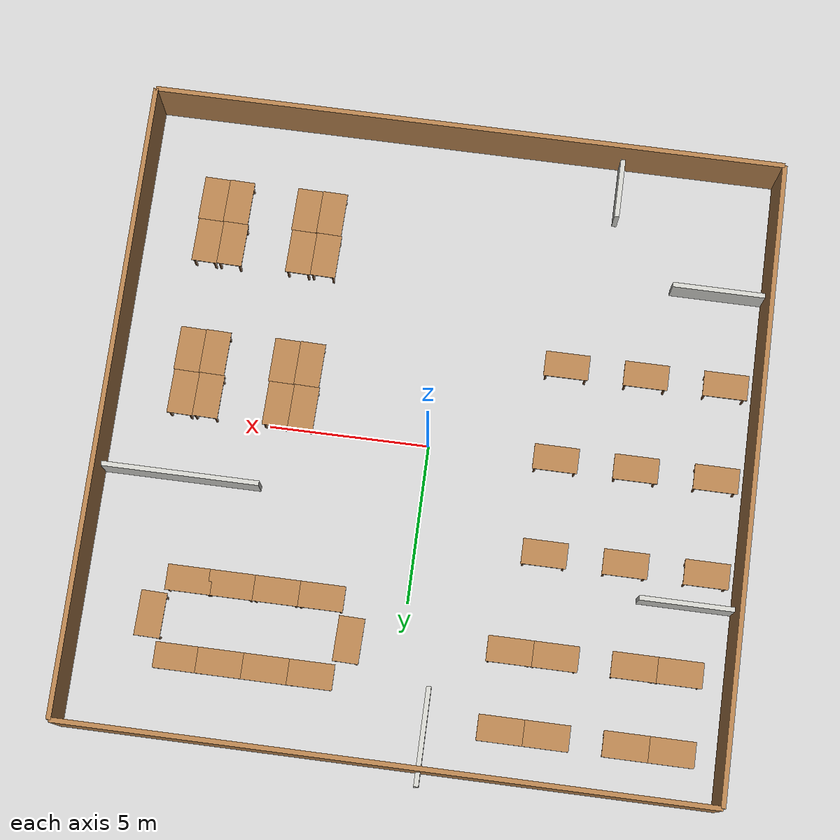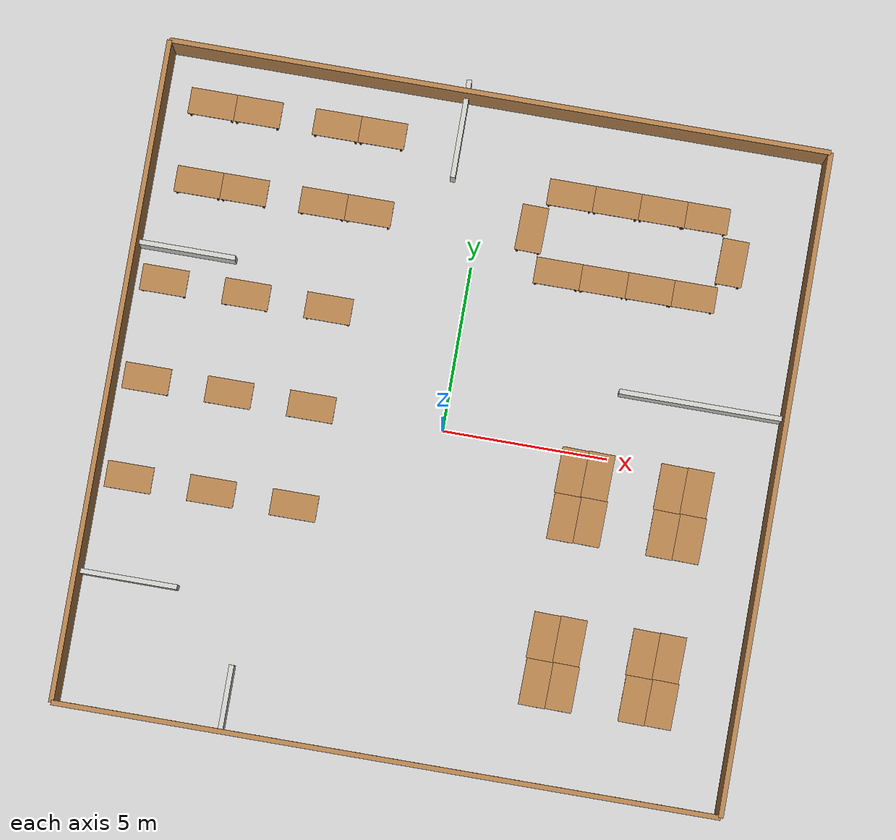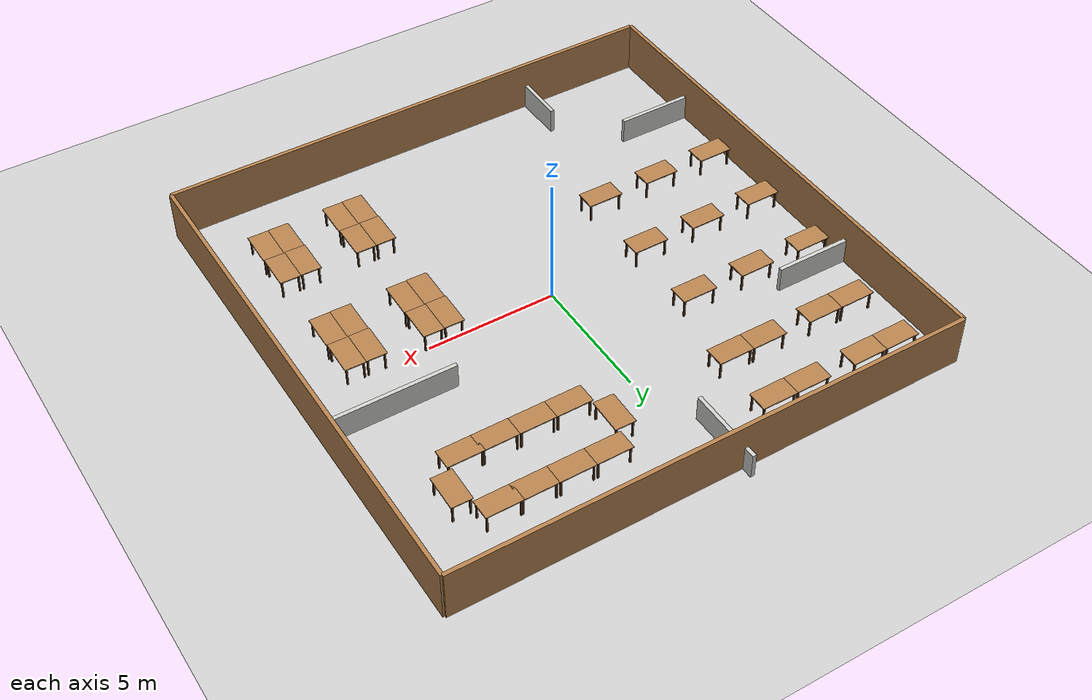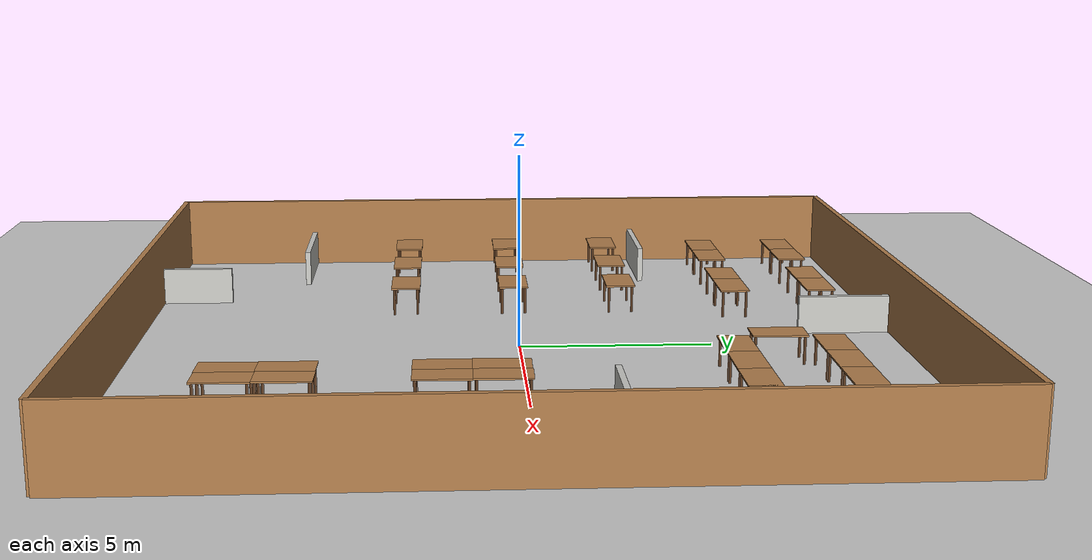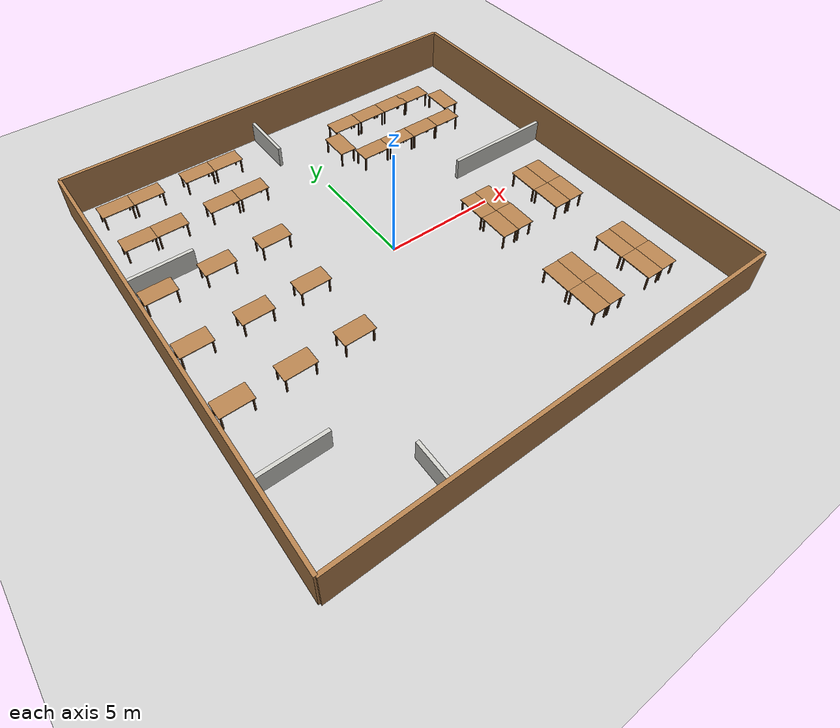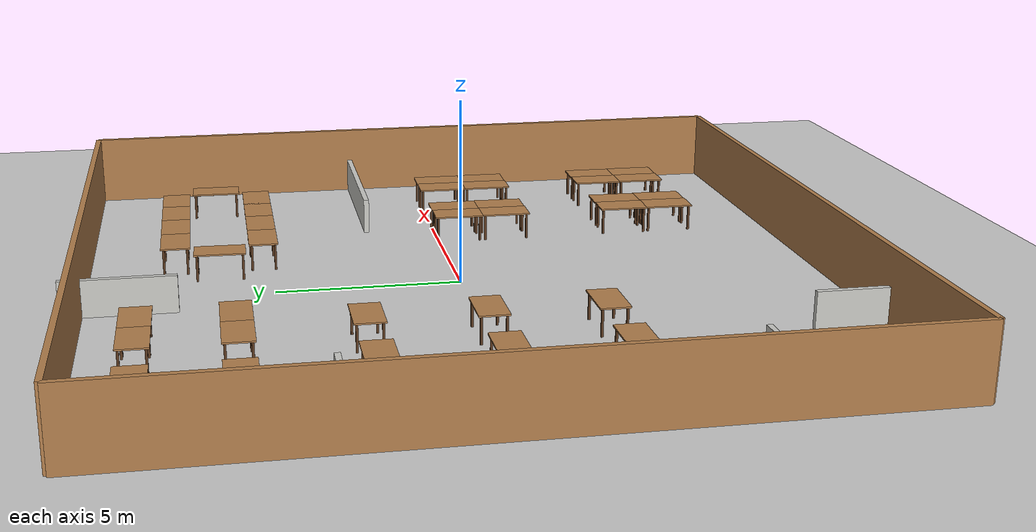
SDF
<sdf version="1.6">
 <world name="restaurant_20x20">
  <light name="sun" type="directional">
   <pose>0 0 10 0 -0 0</pose>
   <diffuse>0.8 0.8 0.8 1</diffuse>
   <specular>0.1 0.1 0.1 1</specular>
   <attenuation>
    <range>1000</range>
    <constant>0.9</constant>
    <linear>0.01</linear>
    <quadratic>0.001</quadratic>
   </attenuation>
   <direction>-0.5 0.5 -1</direction>
  </light>
  <model name="ground_plane">
   <static>1</static>
   <link name="link">
    <collision name="collision">
     <geometry><plane><normal>0 0 1</normal><size>100 100</size></plane></geometry>
     <surface><friction><ode><mu>100</mu><mu2>50</mu2></ode></friction></surface>
    </collision>
    <visual name="visual">
     <cast_shadows>0</cast_shadows>
     <geometry><plane><normal>0 0 1</normal><size>100 100</size></plane></geometry>
     <material>
      <script><uri>file://media/materials/scripts/gazebo.material</uri><name>Gazebo/Grey</name></script>
     </material>
    </visual>
   </link>
  </model>
  <gravity>0 0 -9.8</gravity>
  <physics name="default_physics" default="0" type="ode">
   <max_step_size>0.001</max_step_size>
   <real_time_factor>1</real_time_factor>
   <real_time_update_rate>1000</real_time_update_rate>
  </physics>
  <scene><ambient>0.4 0.4 0.4 1</ambient><background>0.7 0.7 0.7 1</background><shadows>1</shadows></scene>
  <model name="outer_walls">
   <static>1</static>
   <link name="Wall_North">
    <pose>0 10 0 0 0 0</pose>
    <visual name="visual">
     <pose>0 0 1 0 0 0</pose>
     <geometry><box><size>20 0.15 2</size></box></geometry>
     <material>
      <script><uri>file://media/materials/scripts/gazebo.material</uri><name>Gazebo/Wood</name></script>
     </material>
    </visual>
    <collision name="collision">
     <pose>0 0 1 0 0 0</pose>
     <geometry><box><size>20 0.15 2</size></box></geometry>
    </collision>
   </link>
   <link name="Wall_South">
    <pose>0 -10 0 0 0 3.14159</pose>
    <visual name="visual">
     <pose>0 0 1 0 0 0</pose>
     <geometry><box><size>20 0.15 2</size></box></geometry>
     <material>
      <script><uri>file://media/materials/scripts/gazebo.material</uri><name>Gazebo/Wood</name></script>
     </material>
    </visual>
    <collision name="collision">
     <pose>0 0 1 0 0 0</pose>
     <geometry><box><size>20 0.15 2</size></box></geometry>
    </collision>
   </link>
   <link name="Wall_East">
    <pose>10 0 0 0 0 -1.5708</pose>
    <visual name="visual">
     <pose>0 0 1 0 0 0</pose>
     <geometry><box><size>20 0.15 2</size></box></geometry>
     <material>
      <script><uri>file://media/materials/scripts/gazebo.material</uri><name>Gazebo/Wood</name></script>
     </material>
    </visual>
    <collision name="collision">
     <pose>0 0 1 0 0 0</pose>
     <geometry><box><size>20 0.15 2</size></box></geometry>
    </collision>
   </link>
   <link name="Wall_West">
    <pose>-10 0 0 0 0 1.5708</pose>
    <visual name="visual">
     <pose>0 0 1 0 0 0</pose>
     <geometry><box><size>20 0.15 2</size></box></geometry>
     <material>
      <script><uri>file://media/materials/scripts/gazebo.material</uri><name>Gazebo/Wood</name></script>
     </material>
    </visual>
    <collision name="collision">
     <pose>0 0 1 0 0 0</pose>
     <geometry><box><size>20 0.15 2</size></box></geometry>
    </collision>
   </link>
  </model>
  <model name="partition_walls">
   <static>1</static>
   <link name="Wall_Kitchen_North">
    <pose>-8.5 -6 0.5 0 0 0</pose>
    <visual name="visual">
     <geometry><box><size>3 0.15 1</size></box></geometry>
     <material>
      <script><uri>file://media/materials/scripts/gazebo.material</uri><name>Gazebo/CeilingTiled</name></script>
     </material>
    </visual>
    <collision name="collision"><geometry><box><size>5 0.15 1</size></box></geometry></collision>
   </link>
   <link name="Wall_Kitchen_East">
    <pose>-5 -9 0.5 0 0 1.5708</pose>
    <visual name="visual">
     <geometry><box><size>2 0.15 1</size></box></geometry>
     <material>
      <script><uri>file://media/materials/scripts/gazebo.material</uri><name>Gazebo/CeilingTiled</name></script>
     </material>
    </visual>
    <collision name="collision"><geometry><box><size>6 0.15 1</size></box></geometry></collision>
   </link>
   <link name="Wall_Couple_2">
    <pose>-1 9 0.5 0 0 1.5708</pose>
    <visual name="visual">
     <geometry><box><size>3 0.15 1</size></box></geometry>
     <material>
      <script><uri>file://media/materials/scripts/gazebo.material</uri><name>Gazebo/CeilingTiled</name></script>
     </material>
    </visual>
    <collision name="collision"><geometry><box><size>6 0.15 1</size></box></geometry></collision>
   </link>
   <link name="Wall_Couple_1">
    <pose>-8.5 4 0.5 0 0 0</pose>
    <visual name="visual">
     <geometry><box><size>3 0.15 1</size></box></geometry>
     <material>
      <script><uri>file://media/materials/scripts/gazebo.material</uri><name>Gazebo/CeilingTiled</name></script>
     </material>
    </visual>
    <collision name="collision"><geometry><box><size>5 0.15 1</size></box></geometry></collision>
   </link>
   <link name="Wall_meeting">
    <pose>7.5 2 0.5 0 0 0</pose>
    <visual name="visual">
     <geometry><box><size>5 0.15 1</size></box></geometry>
     <material>
      <script><uri>file://media/materials/scripts/gazebo.material</uri><name>Gazebo/CeilingTiled</name></script>
     </material>
    </visual>
    <collision name="collision"><geometry><box><size>5 0.15 1</size></box></geometry></collision>
   </link>
  </model>
  <model name="tables_layout">
   <static>1</static>
   <link name="table_single_1">
    <pose>-9.0 -3.0 0 0 0 0</pose>
    <visual name="top_visual">
     <pose>0 0 0.75 0 0 0</pose>
     <geometry><box><size>1.4 0.8 0.04</size></box></geometry>
     <material>
      <script><uri>file://media/materials/scripts/gazebo.material</uri><name>Gazebo/Wood</name></script>
     </material>
    </visual>
    <collision name="top_collision">
     <pose>0 0 0.75 0 0 0</pose>
     <geometry><box><size>1.4 0.8 0.04</size></box></geometry>
    </collision>
    <visual name="leg_fl_visual">
     <pose>0.62 0.32 0.375 0 0 0</pose>
     <geometry><box><size>0.06 0.06 0.75</size></box></geometry>
     <material><ambient>0.35 0.22 0.12 1</ambient><diffuse>0.35 0.22 0.12 1</diffuse></material>
    </visual>
    <visual name="leg_fr_visual">
     <pose>0.62 -0.32 0.375 0 0 0</pose>
     <geometry><box><size>0.06 0.06 0.75</size></box></geometry>
     <material><ambient>0.35 0.22 0.12 1</ambient><diffuse>0.35 0.22 0.12 1</diffuse></material>
    </visual>
    <visual name="leg_bl_visual">
     <pose>-0.62 0.32 0.375 0 0 0</pose>
     <geometry><box><size>0.06 0.06 0.75</size></box></geometry>
     <material><ambient>0.35 0.22 0.12 1</ambient><diffuse>0.35 0.22 0.12 1</diffuse></material>
    </visual>
    <visual name="leg_br_visual">
     <pose>-0.62 -0.32 0.375 0 0 0</pose>
     <geometry><box><size>0.06 0.06 0.75</size></box></geometry>
     <material><ambient>0.35 0.22 0.12 1</ambient><diffuse>0.35 0.22 0.12 1</diffuse></material>
    </visual>
   </link>
   <link name="table_single_2">
    <pose>-6.5 -3.0 0 0 0 0</pose>
    <visual name="top_visual">
     <pose>0 0 0.75 0 0 0</pose>
     <geometry><box><size>1.4 0.8 0.04</size></box></geometry>
     <material>
      <script><uri>file://media/materials/scripts/gazebo.material</uri><name>Gazebo/Wood</name></script>
     </material>
    </visual>
    <collision name="top_collision">
     <pose>0 0 0.75 0 0 0</pose>
     <geometry><box><size>1.4 0.8 0.04</size></box></geometry>
    </collision>
    <visual name="leg_fl_visual">
     <pose>0.62 0.32 0.375 0 0 0</pose>
     <geometry><box><size>0.06 0.06 0.75</size></box></geometry>
     <material><ambient>0.35 0.22 0.12 1</ambient><diffuse>0.35 0.22 0.12 1</diffuse></material>
    </visual>
    <visual name="leg_fr_visual">
     <pose>0.62 -0.32 0.375 0 0 0</pose>
     <geometry><box><size>0.06 0.06 0.75</size></box></geometry>
     <material><ambient>0.35 0.22 0.12 1</ambient><diffuse>0.35 0.22 0.12 1</diffuse></material>
    </visual>
    <visual name="leg_bl_visual">
     <pose>-0.62 0.32 0.375 0 0 0</pose>
     <geometry><box><size>0.06 0.06 0.75</size></box></geometry>
     <material><ambient>0.35 0.22 0.12 1</ambient><diffuse>0.35 0.22 0.12 1</diffuse></material>
    </visual>
    <visual name="leg_br_visual">
     <pose>-0.62 -0.32 0.375 0 0 0</pose>
     <geometry><box><size>0.06 0.06 0.75</size></box></geometry>
     <material><ambient>0.35 0.22 0.12 1</ambient><diffuse>0.35 0.22 0.12 1</diffuse></material>
    </visual>
   </link>
   <link name="table_single_3">
    <pose>-4.0 -3.0 0 0 0 0</pose>
    <visual name="top_visual">
     <pose>0 0 0.75 0 0 0</pose>
     <geometry><box><size>1.4 0.8 0.04</size></box></geometry>
     <material>
      <script><uri>file://media/materials/scripts/gazebo.material</uri><name>Gazebo/Wood</name></script>
     </material>
    </visual>
    <collision name="top_collision">
     <pose>0 0 0.75 0 0 0</pose>
     <geometry><box><size>1.4 0.8 0.04</size></box></geometry>
    </collision>
    <visual name="leg_fl_visual">
     <pose>0.62 0.32 0.375 0 0 0</pose>
     <geometry><box><size>0.06 0.06 0.75</size></box></geometry>
     <material><ambient>0.35 0.22 0.12 1</ambient><diffuse>0.35 0.22 0.12 1</diffuse></material>
    </visual>
    <visual name="leg_fr_visual">
     <pose>0.62 -0.32 0.375 0 0 0</pose>
     <geometry><box><size>0.06 0.06 0.75</size></box></geometry>
     <material><ambient>0.35 0.22 0.12 1</ambient><diffuse>0.35 0.22 0.12 1</diffuse></material>
    </visual>
    <visual name="leg_bl_visual">
     <pose>-0.62 0.32 0.375 0 0 0</pose>
     <geometry><box><size>0.06 0.06 0.75</size></box></geometry>
     <material><ambient>0.35 0.22 0.12 1</ambient><diffuse>0.35 0.22 0.12 1</diffuse></material>
    </visual>
    <visual name="leg_br_visual">
     <pose>-0.62 -0.32 0.375 0 0 0</pose>
     <geometry><box><size>0.06 0.06 0.75</size></box></geometry>
     <material><ambient>0.35 0.22 0.12 1</ambient><diffuse>0.35 0.22 0.12 1</diffuse></material>
    </visual>
   </link>
   <link name="table_single_4">
    <pose>-9.0 0 0 0 0 0</pose>
    <visual name="top_visual">
     <pose>0 0 0.75 0 0 0</pose>
     <geometry><box><size>1.4 0.8 0.04</size></box></geometry>
     <material>
      <script><uri>file://media/materials/scripts/gazebo.material</uri><name>Gazebo/Wood</name></script>
     </material>
    </visual>
    <collision name="top_collision">
     <pose>0 0 0.75 0 0 0</pose>
     <geometry><box><size>1.4 0.8 0.04</size></box></geometry>
    </collision>
    <visual name="leg_fl_visual">
     <pose>0.62 0.32 0.375 0 0 0</pose>
     <geometry><box><size>0.06 0.06 0.75</size></box></geometry>
     <material><ambient>0.35 0.22 0.12 1</ambient><diffuse>0.35 0.22 0.12 1</diffuse></material>
    </visual>
    <visual name="leg_fr_visual">
     <pose>0.62 -0.32 0.375 0 0 0</pose>
     <geometry><box><size>0.06 0.06 0.75</size></box></geometry>
     <material><ambient>0.35 0.22 0.12 1</ambient><diffuse>0.35 0.22 0.12 1</diffuse></material>
    </visual>
    <visual name="leg_bl_visual">
     <pose>-0.62 0.32 0.375 0 0 0</pose>
     <geometry><box><size>0.06 0.06 0.75</size></box></geometry>
     <material><ambient>0.35 0.22 0.12 1</ambient><diffuse>0.35 0.22 0.12 1</diffuse></material>
    </visual>
    <visual name="leg_br_visual">
     <pose>-0.62 -0.32 0.375 0 0 0</pose>
     <geometry><box><size>0.06 0.06 0.75</size></box></geometry>
     <material><ambient>0.35 0.22 0.12 1</ambient><diffuse>0.35 0.22 0.12 1</diffuse></material>
    </visual>
   </link>
   <link name="table_single_5">
    <pose>-6.5 0 0 0 0 0</pose>
    <visual name="top_visual">
     <pose>0 0 0.75 0 0 0</pose>
     <geometry><box><size>1.4 0.8 0.04</size></box></geometry>
     <material>
      <script><uri>file://media/materials/scripts/gazebo.material</uri><name>Gazebo/Wood</name></script>
     </material>
    </visual>
    <collision name="top_collision">
     <pose>0 0 0.75 0 0 0</pose>
     <geometry><box><size>1.4 0.8 0.04</size></box></geometry>
    </collision>
    <visual name="leg_fl_visual">
     <pose>0.62 0.32 0.375 0 0 0</pose>
     <geometry><box><size>0.06 0.06 0.75</size></box></geometry>
     <material><ambient>0.35 0.22 0.12 1</ambient><diffuse>0.35 0.22 0.12 1</diffuse></material>
    </visual>
    <visual name="leg_fr_visual">
     <pose>0.62 -0.32 0.375 0 0 0</pose>
     <geometry><box><size>0.06 0.06 0.75</size></box></geometry>
     <material><ambient>0.35 0.22 0.12 1</ambient><diffuse>0.35 0.22 0.12 1</diffuse></material>
    </visual>
    <visual name="leg_bl_visual">
     <pose>-0.62 0.32 0.375 0 0 0</pose>
     <geometry><box><size>0.06 0.06 0.75</size></box></geometry>
     <material><ambient>0.35 0.22 0.12 1</ambient><diffuse>0.35 0.22 0.12 1</diffuse></material>
    </visual>
    <visual name="leg_br_visual">
     <pose>-0.62 -0.32 0.375 0 0 0</pose>
     <geometry><box><size>0.06 0.06 0.75</size></box></geometry>
     <material><ambient>0.35 0.22 0.12 1</ambient><diffuse>0.35 0.22 0.12 1</diffuse></material>
    </visual>
   </link>
   <link name="table_single_6">
    <pose>-4.0 0 0 0 0 0</pose>
    <visual name="top_visual">
     <pose>0 0 0.75 0 0 0</pose>
     <geometry><box><size>1.4 0.8 0.04</size></box></geometry>
     <material>
      <script><uri>file://media/materials/scripts/gazebo.material</uri><name>Gazebo/Wood</name></script>
     </material>
    </visual>
    <collision name="top_collision">
     <pose>0 0 0.75 0 0 0</pose>
     <geometry><box><size>1.4 0.8 0.04</size></box></geometry>
    </collision>
    <visual name="leg_fl_visual">
     <pose>0.62 0.32 0.375 0 0 0</pose>
     <geometry><box><size>0.06 0.06 0.75</size></box></geometry>
     <material><ambient>0.35 0.22 0.12 1</ambient><diffuse>0.35 0.22 0.12 1</diffuse></material>
    </visual>
    <visual name="leg_fr_visual">
     <pose>0.62 -0.32 0.375 0 0 0</pose>
     <geometry><box><size>0.06 0.06 0.75</size></box></geometry>
     <material><ambient>0.35 0.22 0.12 1</ambient><diffuse>0.35 0.22 0.12 1</diffuse></material>
    </visual>
    <visual name="leg_bl_visual">
     <pose>-0.62 0.32 0.375 0 0 0</pose>
     <geometry><box><size>0.06 0.06 0.75</size></box></geometry>
     <material><ambient>0.35 0.22 0.12 1</ambient><diffuse>0.35 0.22 0.12 1</diffuse></material>
    </visual>
    <visual name="leg_br_visual">
     <pose>-0.62 -0.32 0.375 0 0 0</pose>
     <geometry><box><size>0.06 0.06 0.75</size></box></geometry>
     <material><ambient>0.35 0.22 0.12 1</ambient><diffuse>0.35 0.22 0.12 1</diffuse></material>
    </visual>
   </link>
   <link name="table_single_7">
    <pose>-9.0 3.0 0 0 0 0</pose>
    <visual name="top_visual">
     <pose>0 0 0.75 0 0 0</pose>
     <geometry><box><size>1.4 0.8 0.04</size></box></geometry>
     <material>
      <script><uri>file://media/materials/scripts/gazebo.material</uri><name>Gazebo/Wood</name></script>
     </material>
    </visual>
    <collision name="top_collision">
     <pose>0 0 0.75 0 0 0</pose>
     <geometry><box><size>1.4 0.8 0.04</size></box></geometry>
    </collision>
    <visual name="leg_fl_visual">
     <pose>0.62 0.32 0.375 0 0 0</pose>
     <geometry><box><size>0.06 0.06 0.75</size></box></geometry>
     <material><ambient>0.35 0.22 0.12 1</ambient><diffuse>0.35 0.22 0.12 1</diffuse></material>
    </visual>
    <visual name="leg_fr_visual">
     <pose>0.62 -0.32 0.375 0 0 0</pose>
     <geometry><box><size>0.06 0.06 0.75</size></box></geometry>
     <material><ambient>0.35 0.22 0.12 1</ambient><diffuse>0.35 0.22 0.12 1</diffuse></material>
    </visual>
    <visual name="leg_bl_visual">
     <pose>-0.62 0.32 0.375 0 0 0</pose>
     <geometry><box><size>0.06 0.06 0.75</size></box></geometry>
     <material><ambient>0.35 0.22 0.12 1</ambient><diffuse>0.35 0.22 0.12 1</diffuse></material>
    </visual>
    <visual name="leg_br_visual">
     <pose>-0.62 -0.32 0.375 0 0 0</pose>
     <geometry><box><size>0.06 0.06 0.75</size></box></geometry>
     <material><ambient>0.35 0.22 0.12 1</ambient><diffuse>0.35 0.22 0.12 1</diffuse></material>
    </visual>
   </link>
   <link name="table_single_8">
    <pose>-6.5 3.0 0 0 0 0</pose>
    <visual name="top_visual">
     <pose>0 0 0.75 0 0 0</pose>
     <geometry><box><size>1.4 0.8 0.04</size></box></geometry>
     <material>
      <script><uri>file://media/materials/scripts/gazebo.material</uri><name>Gazebo/Wood</name></script>
     </material>
    </visual>
    <collision name="top_collision">
     <pose>0 0 0.75 0 0 0</pose>
     <geometry><box><size>1.4 0.8 0.04</size></box></geometry>
    </collision>
    <visual name="leg_fl_visual">
     <pose>0.62 0.32 0.375 0 0 0</pose>
     <geometry><box><size>0.06 0.06 0.75</size></box></geometry>
     <material><ambient>0.35 0.22 0.12 1</ambient><diffuse>0.35 0.22 0.12 1</diffuse></material>
    </visual>
    <visual name="leg_fr_visual">
     <pose>0.62 -0.32 0.375 0 0 0</pose>
     <geometry><box><size>0.06 0.06 0.75</size></box></geometry>
     <material><ambient>0.35 0.22 0.12 1</ambient><diffuse>0.35 0.22 0.12 1</diffuse></material>
    </visual>
    <visual name="leg_bl_visual">
     <pose>-0.62 0.32 0.375 0 0 0</pose>
     <geometry><box><size>0.06 0.06 0.75</size></box></geometry>
     <material><ambient>0.35 0.22 0.12 1</ambient><diffuse>0.35 0.22 0.12 1</diffuse></material>
    </visual>
    <visual name="leg_br_visual">
     <pose>-0.62 -0.32 0.375 0 0 0</pose>
     <geometry><box><size>0.06 0.06 0.75</size></box></geometry>
     <material><ambient>0.35 0.22 0.12 1</ambient><diffuse>0.35 0.22 0.12 1</diffuse></material>
    </visual>
   </link>
   <link name="table_single_9">
    <pose>-4.0 3.0 0 0 0 0</pose>
    <visual name="top_visual">
     <pose>0 0 0.75 0 0 0</pose>
     <geometry><box><size>1.4 0.8 0.04</size></box></geometry>
     <material>
      <script><uri>file://media/materials/scripts/gazebo.material</uri><name>Gazebo/Wood</name></script>
     </material>
    </visual>
    <collision name="top_collision">
     <pose>0 0 0.75 0 0 0</pose>
     <geometry><box><size>1.4 0.8 0.04</size></box></geometry>
    </collision>
    <visual name="leg_fl_visual">
     <pose>0.62 0.32 0.375 0 0 0</pose>
     <geometry><box><size>0.06 0.06 0.75</size></box></geometry>
     <material><ambient>0.35 0.22 0.12 1</ambient><diffuse>0.35 0.22 0.12 1</diffuse></material>
    </visual>
    <visual name="leg_fr_visual">
     <pose>0.62 -0.32 0.375 0 0 0</pose>
     <geometry><box><size>0.06 0.06 0.75</size></box></geometry>
     <material><ambient>0.35 0.22 0.12 1</ambient><diffuse>0.35 0.22 0.12 1</diffuse></material>
    </visual>
    <visual name="leg_bl_visual">
     <pose>-0.62 0.32 0.375 0 0 0</pose>
     <geometry><box><size>0.06 0.06 0.75</size></box></geometry>
     <material><ambient>0.35 0.22 0.12 1</ambient><diffuse>0.35 0.22 0.12 1</diffuse></material>
    </visual>
    <visual name="leg_br_visual">
     <pose>-0.62 -0.32 0.375 0 0 0</pose>
     <geometry><box><size>0.06 0.06 0.75</size></box></geometry>
     <material><ambient>0.35 0.22 0.12 1</ambient><diffuse>0.35 0.22 0.12 1</diffuse></material>
    </visual>
   </link>
   <link name="table_couple_1">
    <pose>-8.5 8.5 0 0 0 0</pose>
    <visual name="top_visual">
     <pose>0 0 0.75 0 0 0</pose>
     <geometry><box><size>1.4 0.8 0.04</size></box></geometry>
     <material>
      <script><uri>file://media/materials/scripts/gazebo.material</uri><name>Gazebo/Wood</name></script>
     </material>
    </visual>
    <collision name="top_collision">
     <pose>0 0 0.75 0 0 0</pose>
     <geometry><box><size>1.4 0.8 0.04</size></box></geometry>
    </collision>
    <visual name="leg_fl_visual">
     <pose>0.62 0.32 0.375 0 0 0</pose>
     <geometry><box><size>0.06 0.06 0.75</size></box></geometry>
     <material><ambient>0.35 0.22 0.12 1</ambient><diffuse>0.35 0.22 0.12 1</diffuse></material>
    </visual>
    <visual name="leg_fr_visual">
     <pose>0.62 -0.32 0.375 0 0 0</pose>
     <geometry><box><size>0.06 0.06 0.75</size></box></geometry>
     <material><ambient>0.35 0.22 0.12 1</ambient><diffuse>0.35 0.22 0.12 1</diffuse></material>
    </visual>
    <visual name="leg_bl_visual">
     <pose>-0.62 0.32 0.375 0 0 0</pose>
     <geometry><box><size>0.06 0.06 0.75</size></box></geometry>
     <material><ambient>0.35 0.22 0.12 1</ambient><diffuse>0.35 0.22 0.12 1</diffuse></material>
    </visual>
    <visual name="leg_br_visual">
     <pose>-0.62 -0.32 0.375 0 0 0</pose>
     <geometry><box><size>0.06 0.06 0.75</size></box></geometry>
     <material><ambient>0.35 0.22 0.12 1</ambient><diffuse>0.35 0.22 0.12 1</diffuse></material>
    </visual>
   </link>
   <link name="table_couple_2">
    <pose>-7.1 8.5 0 0 0 0</pose>
    <visual name="top_visual">
     <pose>0 0 0.75 0 0 0</pose>
     <geometry><box><size>1.4 0.8 0.04</size></box></geometry>
     <material>
      <script><uri>file://media/materials/scripts/gazebo.material</uri><name>Gazebo/Wood</name></script>
     </material>
    </visual>
    <collision name="top_collision">
     <pose>0 0 0.75 0 0 0</pose>
     <geometry><box><size>1.4 0.8 0.04</size></box></geometry>
    </collision>
    <visual name="leg_fl_visual">
     <pose>0.62 0.32 0.375 0 0 0</pose>
     <geometry><box><size>0.06 0.06 0.75</size></box></geometry>
     <material><ambient>0.35 0.22 0.12 1</ambient><diffuse>0.35 0.22 0.12 1</diffuse></material>
    </visual>
    <visual name="leg_fr_visual">
     <pose>0.62 -0.32 0.375 0 0 0</pose>
     <geometry><box><size>0.06 0.06 0.75</size></box></geometry>
     <material><ambient>0.35 0.22 0.12 1</ambient><diffuse>0.35 0.22 0.12 1</diffuse></material>
    </visual>
    <visual name="leg_bl_visual">
     <pose>-0.62 0.32 0.375 0 0 0</pose>
     <geometry><box><size>0.06 0.06 0.75</size></box></geometry>
     <material><ambient>0.35 0.22 0.12 1</ambient><diffuse>0.35 0.22 0.12 1</diffuse></material>
    </visual>
    <visual name="leg_br_visual">
     <pose>-0.62 -0.32 0.375 0 0 0</pose>
     <geometry><box><size>0.06 0.06 0.75</size></box></geometry>
     <material><ambient>0.35 0.22 0.12 1</ambient><diffuse>0.35 0.22 0.12 1</diffuse></material>
    </visual>
   </link>
   <link name="table_couple_3">
    <pose>-8.5 6.1 0 0 0 0</pose>
    <visual name="top_visual">
     <pose>0 0 0.75 0 0 0</pose>
     <geometry><box><size>1.4 0.8 0.04</size></box></geometry>
     <material>
      <script><uri>file://media/materials/scripts/gazebo.material</uri><name>Gazebo/Wood</name></script>
     </material>
    </visual>
    <collision name="top_collision">
     <pose>0 0 0.75 0 0 0</pose>
     <geometry><box><size>1.4 0.8 0.04</size></box></geometry>
    </collision>
    <visual name="leg_fl_visual">
     <pose>0.62 0.32 0.375 0 0 0</pose>
     <geometry><box><size>0.06 0.06 0.75</size></box></geometry>
     <material><ambient>0.35 0.22 0.12 1</ambient><diffuse>0.35 0.22 0.12 1</diffuse></material>
    </visual>
    <visual name="leg_fr_visual">
     <pose>0.62 -0.32 0.375 0 0 0</pose>
     <geometry><box><size>0.06 0.06 0.75</size></box></geometry>
     <material><ambient>0.35 0.22 0.12 1</ambient><diffuse>0.35 0.22 0.12 1</diffuse></material>
    </visual>
    <visual name="leg_bl_visual">
     <pose>-0.62 0.32 0.375 0 0 0</pose>
     <geometry><box><size>0.06 0.06 0.75</size></box></geometry>
     <material><ambient>0.35 0.22 0.12 1</ambient><diffuse>0.35 0.22 0.12 1</diffuse></material>
    </visual>
    <visual name="leg_br_visual">
     <pose>-0.62 -0.32 0.375 0 0 0</pose>
     <geometry><box><size>0.06 0.06 0.75</size></box></geometry>
     <material><ambient>0.35 0.22 0.12 1</ambient><diffuse>0.35 0.22 0.12 1</diffuse></material>
    </visual>
   </link>
   <link name="table_couple_4">
    <pose>-7.1 6.1 0 0 0 0</pose>
    <visual name="top_visual">
     <pose>0 0 0.75 0 0 0</pose>
     <geometry><box><size>1.4 0.8 0.04</size></box></geometry>
     <material>
      <script><uri>file://media/materials/scripts/gazebo.material</uri><name>Gazebo/Wood</name></script>
     </material>
    </visual>
    <collision name="top_collision">
     <pose>0 0 0.75 0 0 0</pose>
     <geometry><box><size>1.4 0.8 0.04</size></box></geometry>
    </collision>
    <visual name="leg_fl_visual">
     <pose>0.62 0.32 0.375 0 0 0</pose>
     <geometry><box><size>0.06 0.06 0.75</size></box></geometry>
     <material><ambient>0.35 0.22 0.12 1</ambient><diffuse>0.35 0.22 0.12 1</diffuse></material>
    </visual>
    <visual name="leg_fr_visual">
     <pose>0.62 -0.32 0.375 0 0 0</pose>
     <geometry><box><size>0.06 0.06 0.75</size></box></geometry>
     <material><ambient>0.35 0.22 0.12 1</ambient><diffuse>0.35 0.22 0.12 1</diffuse></material>
    </visual>
    <visual name="leg_bl_visual">
     <pose>-0.62 0.32 0.375 0 0 0</pose>
     <geometry><box><size>0.06 0.06 0.75</size></box></geometry>
     <material><ambient>0.35 0.22 0.12 1</ambient><diffuse>0.35 0.22 0.12 1</diffuse></material>
    </visual>
    <visual name="leg_br_visual">
     <pose>-0.62 -0.32 0.375 0 0 0</pose>
     <geometry><box><size>0.06 0.06 0.75</size></box></geometry>
     <material><ambient>0.35 0.22 0.12 1</ambient><diffuse>0.35 0.22 0.12 1</diffuse></material>
    </visual>
   </link>
   <link name="table_couple_5">
    <pose>-4.7 8.5 0 0 0 0</pose>
    <visual name="top_visual">
     <pose>0 0 0.75 0 0 0</pose>
     <geometry><box><size>1.4 0.8 0.04</size></box></geometry>
     <material>
      <script><uri>file://media/materials/scripts/gazebo.material</uri><name>Gazebo/Wood</name></script>
     </material>
    </visual>
    <collision name="top_collision">
     <pose>0 0 0.75 0 0 0</pose>
     <geometry><box><size>1.4 0.8 0.04</size></box></geometry>
    </collision>
    <visual name="leg_fl_visual">
     <pose>0.62 0.32 0.375 0 0 0</pose>
     <geometry><box><size>0.06 0.06 0.75</size></box></geometry>
     <material><ambient>0.35 0.22 0.12 1</ambient><diffuse>0.35 0.22 0.12 1</diffuse></material>
    </visual>
    <visual name="leg_fr_visual">
     <pose>0.62 -0.32 0.375 0 0 0</pose>
     <geometry><box><size>0.06 0.06 0.75</size></box></geometry>
     <material><ambient>0.35 0.22 0.12 1</ambient><diffuse>0.35 0.22 0.12 1</diffuse></material>
    </visual>
    <visual name="leg_bl_visual">
     <pose>-0.62 0.32 0.375 0 0 0</pose>
     <geometry><box><size>0.06 0.06 0.75</size></box></geometry>
     <material><ambient>0.35 0.22 0.12 1</ambient><diffuse>0.35 0.22 0.12 1</diffuse></material>
    </visual>
    <visual name="leg_br_visual">
     <pose>-0.62 -0.32 0.375 0 0 0</pose>
     <geometry><box><size>0.06 0.06 0.75</size></box></geometry>
     <material><ambient>0.35 0.22 0.12 1</ambient><diffuse>0.35 0.22 0.12 1</diffuse></material>
    </visual>
   </link>
   <link name="table_couple_6">
    <pose>-3.3 8.5 0 0 0 0</pose>
    <visual name="top_visual">
     <pose>0 0 0.75 0 0 0</pose>
     <geometry><box><size>1.4 0.8 0.04</size></box></geometry>
     <material>
      <script><uri>file://media/materials/scripts/gazebo.material</uri><name>Gazebo/Wood</name></script>
     </material>
    </visual>
    <collision name="top_collision">
     <pose>0 0 0.75 0 0 0</pose>
     <geometry><box><size>1.4 0.8 0.04</size></box></geometry>
    </collision>
    <visual name="leg_fl_visual">
     <pose>0.62 0.32 0.375 0 0 0</pose>
     <geometry><box><size>0.06 0.06 0.75</size></box></geometry>
     <material><ambient>0.35 0.22 0.12 1</ambient><diffuse>0.35 0.22 0.12 1</diffuse></material>
    </visual>
    <visual name="leg_fr_visual">
     <pose>0.62 -0.32 0.375 0 0 0</pose>
     <geometry><box><size>0.06 0.06 0.75</size></box></geometry>
     <material><ambient>0.35 0.22 0.12 1</ambient><diffuse>0.35 0.22 0.12 1</diffuse></material>
    </visual>
    <visual name="leg_bl_visual">
     <pose>-0.62 0.32 0.375 0 0 0</pose>
     <geometry><box><size>0.06 0.06 0.75</size></box></geometry>
     <material><ambient>0.35 0.22 0.12 1</ambient><diffuse>0.35 0.22 0.12 1</diffuse></material>
    </visual>
    <visual name="leg_br_visual">
     <pose>-0.62 -0.32 0.375 0 0 0</pose>
     <geometry><box><size>0.06 0.06 0.75</size></box></geometry>
     <material><ambient>0.35 0.22 0.12 1</ambient><diffuse>0.35 0.22 0.12 1</diffuse></material>
    </visual>
   </link>
   <link name="table_couple_7">
    <pose>-4.7 6.1 0 0 0 0</pose>
    <visual name="top_visual">
     <pose>0 0 0.75 0 0 0</pose>
     <geometry><box><size>1.4 0.8 0.04</size></box></geometry>
     <material>
      <script><uri>file://media/materials/scripts/gazebo.material</uri><name>Gazebo/Wood</name></script>
     </material>
    </visual>
    <collision name="top_collision">
     <pose>0 0 0.75 0 0 0</pose>
     <geometry><box><size>1.4 0.8 0.04</size></box></geometry>
    </collision>
    <visual name="leg_fl_visual">
     <pose>0.62 0.32 0.375 0 0 0</pose>
     <geometry><box><size>0.06 0.06 0.75</size></box></geometry>
     <material><ambient>0.35 0.22 0.12 1</ambient><diffuse>0.35 0.22 0.12 1</diffuse></material>
    </visual>
    <visual name="leg_fr_visual">
     <pose>0.62 -0.32 0.375 0 0 0</pose>
     <geometry><box><size>0.06 0.06 0.75</size></box></geometry>
     <material><ambient>0.35 0.22 0.12 1</ambient><diffuse>0.35 0.22 0.12 1</diffuse></material>
    </visual>
    <visual name="leg_bl_visual">
     <pose>-0.62 0.32 0.375 0 0 0</pose>
     <geometry><box><size>0.06 0.06 0.75</size></box></geometry>
     <material><ambient>0.35 0.22 0.12 1</ambient><diffuse>0.35 0.22 0.12 1</diffuse></material>
    </visual>
    <visual name="leg_br_visual">
     <pose>-0.62 -0.32 0.375 0 0 0</pose>
     <geometry><box><size>0.06 0.06 0.75</size></box></geometry>
     <material><ambient>0.35 0.22 0.12 1</ambient><diffuse>0.35 0.22 0.12 1</diffuse></material>
    </visual>
   </link>
   <link name="table_couple_8">
    <pose>-3.3 6.1 0 0 0 0</pose>
    <visual name="top_visual">
     <pose>0 0 0.75 0 0 0</pose>
     <geometry><box><size>1.4 0.8 0.04</size></box></geometry>
     <material>
      <script><uri>file://media/materials/scripts/gazebo.material</uri><name>Gazebo/Wood</name></script>
     </material>
    </visual>
    <collision name="top_collision">
     <pose>0 0 0.75 0 0 0</pose>
     <geometry><box><size>1.4 0.8 0.04</size></box></geometry>
    </collision>
    <visual name="leg_fl_visual">
     <pose>0.62 0.32 0.375 0 0 0</pose>
     <geometry><box><size>0.06 0.06 0.75</size></box></geometry>
     <material><ambient>0.35 0.22 0.12 1</ambient><diffuse>0.35 0.22 0.12 1</diffuse></material>
    </visual>
    <visual name="leg_fr_visual">
     <pose>0.62 -0.32 0.375 0 0 0</pose>
     <geometry><box><size>0.06 0.06 0.75</size></box></geometry>
     <material><ambient>0.35 0.22 0.12 1</ambient><diffuse>0.35 0.22 0.12 1</diffuse></material>
    </visual>
    <visual name="leg_bl_visual">
     <pose>-0.62 0.32 0.375 0 0 0</pose>
     <geometry><box><size>0.06 0.06 0.75</size></box></geometry>
     <material><ambient>0.35 0.22 0.12 1</ambient><diffuse>0.35 0.22 0.12 1</diffuse></material>
    </visual>
    <visual name="leg_br_visual">
     <pose>-0.62 -0.32 0.375 0 0 0</pose>
     <geometry><box><size>0.06 0.06 0.75</size></box></geometry>
     <material><ambient>0.35 0.22 0.12 1</ambient><diffuse>0.35 0.22 0.12 1</diffuse></material>
    </visual>
   </link>
   <link name="banquet_1">
    <pose>7.0 -7.0 0 0 0 1.550</pose>
    <visual name="top_visual">
     <pose>0 0 0.75 0 0 0</pose>
     <geometry><box><size>1.4 0.8 0.04</size></box></geometry>
     <material>
      <script><uri>file://media/materials/scripts/gazebo.material</uri><name>Gazebo/Wood</name></script>
     </material>
    </visual>
    <collision name="top_collision">
     <pose>0 0 0.75 0 0 0</pose>
     <geometry><box><size>1.4 0.8 0.04</size></box></geometry>
    </collision>
    <visual name="leg_fl_visual">
     <pose>0.62 0.32 0.375 0 0 0</pose>
     <geometry><box><size>0.06 0.06 0.75</size></box></geometry>
     <material><ambient>0.35 0.22 0.12 1</ambient><diffuse>0.35 0.22 0.12 1</diffuse></material>
    </visual>
    <visual name="leg_fr_visual">
     <pose>0.62 -0.32 0.375 0 0 0</pose>
     <geometry><box><size>0.06 0.06 0.75</size></box></geometry>
     <material><ambient>0.35 0.22 0.12 1</ambient><diffuse>0.35 0.22 0.12 1</diffuse></material>
    </visual>
    <visual name="leg_bl_visual">
     <pose>-0.62 0.32 0.375 0 0 0</pose>
     <geometry><box><size>0.06 0.06 0.75</size></box></geometry>
     <material><ambient>0.35 0.22 0.12 1</ambient><diffuse>0.35 0.22 0.12 1</diffuse></material>
    </visual>
    <visual name="leg_br_visual">
     <pose>-0.62 -0.32 0.375 0 0 0</pose>
     <geometry><box><size>0.06 0.06 0.75</size></box></geometry>
     <material><ambient>0.35 0.22 0.12 1</ambient><diffuse>0.35 0.22 0.12 1</diffuse></material>
    </visual>
   </link>
   <link name="banquet_2">
    <pose>7.8 -7.0 0 0 0 1.550</pose>
    <visual name="top_visual">
     <pose>0 0 0.75 0 0 0</pose>
     <geometry><box><size>1.4 0.8 0.04</size></box></geometry>
     <material>
      <script><uri>file://media/materials/scripts/gazebo.material</uri><name>Gazebo/Wood</name></script>
     </material>
    </visual>
    <collision name="top_collision">
     <pose>0 0 0.75 0 0 0</pose>
     <geometry><box><size>1.4 0.8 0.04</size></box></geometry>
    </collision>
    <visual name="leg_fl_visual">
     <pose>0.62 0.32 0.375 0 0 0</pose>
     <geometry><box><size>0.06 0.06 0.75</size></box></geometry>
     <material><ambient>0.35 0.22 0.12 1</ambient><diffuse>0.35 0.22 0.12 1</diffuse></material>
    </visual>
    <visual name="leg_fr_visual">
     <pose>0.62 -0.32 0.375 0 0 0</pose>
     <geometry><box><size>0.06 0.06 0.75</size></box></geometry>
     <material><ambient>0.35 0.22 0.12 1</ambient><diffuse>0.35 0.22 0.12 1</diffuse></material>
    </visual>
    <visual name="leg_bl_visual">
     <pose>-0.62 0.32 0.375 0 0 0</pose>
     <geometry><box><size>0.06 0.06 0.75</size></box></geometry>
     <material><ambient>0.35 0.22 0.12 1</ambient><diffuse>0.35 0.22 0.12 1</diffuse></material>
    </visual>
    <visual name="leg_br_visual">
     <pose>-0.62 -0.32 0.375 0 0 0</pose>
     <geometry><box><size>0.06 0.06 0.75</size></box></geometry>
     <material><ambient>0.35 0.22 0.12 1</ambient><diffuse>0.35 0.22 0.12 1</diffuse></material>
    </visual>
   </link>
   <link name="banquet_3">
    <pose>7.0 -5.6 0 0 0 1.550</pose>
    <visual name="top_visual">
     <pose>0 0 0.75 0 0 0</pose>
     <geometry><box><size>1.4 0.8 0.04</size></box></geometry>
     <material>
      <script><uri>file://media/materials/scripts/gazebo.material</uri><name>Gazebo/Wood</name></script>
     </material>
    </visual>
    <collision name="top_collision">
     <pose>0 0 0.75 0 0 0</pose>
     <geometry><box><size>1.4 0.8 0.04</size></box></geometry>
    </collision>
    <visual name="leg_fl_visual">
     <pose>0.62 0.32 0.375 0 0 0</pose>
     <geometry><box><size>0.06 0.06 0.75</size></box></geometry>
     <material><ambient>0.35 0.22 0.12 1</ambient><diffuse>0.35 0.22 0.12 1</diffuse></material>
    </visual>
    <visual name="leg_fr_visual">
     <pose>0.62 -0.32 0.375 0 0 0</pose>
     <geometry><box><size>0.06 0.06 0.75</size></box></geometry>
     <material><ambient>0.35 0.22 0.12 1</ambient><diffuse>0.35 0.22 0.12 1</diffuse></material>
    </visual>
    <visual name="leg_bl_visual">
     <pose>-0.62 0.32 0.375 0 0 0</pose>
     <geometry><box><size>0.06 0.06 0.75</size></box></geometry>
     <material><ambient>0.35 0.22 0.12 1</ambient><diffuse>0.35 0.22 0.12 1</diffuse></material>
    </visual>
    <visual name="leg_br_visual">
     <pose>-0.62 -0.32 0.375 0 0 0</pose>
     <geometry><box><size>0.06 0.06 0.75</size></box></geometry>
     <material><ambient>0.35 0.22 0.12 1</ambient><diffuse>0.35 0.22 0.12 1</diffuse></material>
    </visual>
   </link>
   <link name="banquet_4">
    <pose>7.8 -5.6 0 0 0 1.550</pose>
    <visual name="top_visual">
     <pose>0 0 0.75 0 0 0</pose>
     <geometry><box><size>1.4 0.8 0.04</size></box></geometry>
     <material>
      <script><uri>file://media/materials/scripts/gazebo.material</uri><name>Gazebo/Wood</name></script>
     </material>
    </visual>
    <collision name="top_collision">
     <pose>0 0 0.75 0 0 0</pose>
     <geometry><box><size>1.4 0.8 0.04</size></box></geometry>
    </collision>
    <visual name="leg_fl_visual">
     <pose>0.62 0.32 0.375 0 0 0</pose>
     <geometry><box><size>0.06 0.06 0.75</size></box></geometry>
     <material><ambient>0.35 0.22 0.12 1</ambient><diffuse>0.35 0.22 0.12 1</diffuse></material>
    </visual>
    <visual name="leg_fr_visual">
     <pose>0.62 -0.32 0.375 0 0 0</pose>
     <geometry><box><size>0.06 0.06 0.75</size></box></geometry>
     <material><ambient>0.35 0.22 0.12 1</ambient><diffuse>0.35 0.22 0.12 1</diffuse></material>
    </visual>
    <visual name="leg_bl_visual">
     <pose>-0.62 0.32 0.375 0 0 0</pose>
     <geometry><box><size>0.06 0.06 0.75</size></box></geometry>
     <material><ambient>0.35 0.22 0.12 1</ambient><diffuse>0.35 0.22 0.12 1</diffuse></material>
    </visual>
    <visual name="leg_br_visual">
     <pose>-0.62 -0.32 0.375 0 0 0</pose>
     <geometry><box><size>0.06 0.06 0.75</size></box></geometry>
     <material><ambient>0.35 0.22 0.12 1</ambient><diffuse>0.35 0.22 0.12 1</diffuse></material>
    </visual>
   </link>
   <link name="banquet_5">
    <pose>7.0 -2 0 0 0 1.550</pose>
    <visual name="top_visual">
     <pose>0 0 0.75 0 0 0</pose>
     <geometry><box><size>1.4 0.8 0.04</size></box></geometry>
     <material>
      <script><uri>file://media/materials/scripts/gazebo.material</uri><name>Gazebo/Wood</name></script>
     </material>
    </visual>
    <collision name="top_collision">
     <pose>0 0 0.75 0 0 0</pose>
     <geometry><box><size>1.4 0.8 0.04</size></box></geometry>
    </collision>
    <visual name="leg_fl_visual">
     <pose>0.62 0.32 0.375 0 0 0</pose>
     <geometry><box><size>0.06 0.06 0.75</size></box></geometry>
     <material><ambient>0.35 0.22 0.12 1</ambient><diffuse>0.35 0.22 0.12 1</diffuse></material>
    </visual>
    <visual name="leg_fr_visual">
     <pose>0.62 -0.32 0.375 0 0 0</pose>
     <geometry><box><size>0.06 0.06 0.75</size></box></geometry>
     <material><ambient>0.35 0.22 0.12 1</ambient><diffuse>0.35 0.22 0.12 1</diffuse></material>
    </visual>
    <visual name="leg_bl_visual">
     <pose>-0.62 0.32 0.375 0 0 0</pose>
     <geometry><box><size>0.06 0.06 0.75</size></box></geometry>
     <material><ambient>0.35 0.22 0.12 1</ambient><diffuse>0.35 0.22 0.12 1</diffuse></material>
    </visual>
    <visual name="leg_br_visual">
     <pose>-0.62 -0.32 0.375 0 0 0</pose>
     <geometry><box><size>0.06 0.06 0.75</size></box></geometry>
     <material><ambient>0.35 0.22 0.12 1</ambient><diffuse>0.35 0.22 0.12 1</diffuse></material>
    </visual>
   </link>
   <link name="banquet_6">
    <pose>7.8 -2 0 0 0 1.5500</pose>
    <visual name="top_visual">
     <pose>0 0 0.75 0 0 0</pose>
     <geometry><box><size>1.4 0.8 0.04</size></box></geometry>
     <material>
      <script><uri>file://media/materials/scripts/gazebo.material</uri><name>Gazebo/Wood</name></script>
     </material>
    </visual>
    <collision name="top_collision">
     <pose>0 0 0.75 0 0 0</pose>
     <geometry><box><size>1.4 0.8 0.04</size></box></geometry>
    </collision>
    <visual name="leg_fl_visual">
     <pose>0.62 0.32 0.375 0 0 0</pose>
     <geometry><box><size>0.06 0.06 0.75</size></box></geometry>
     <material><ambient>0.35 0.22 0.12 1</ambient><diffuse>0.35 0.22 0.12 1</diffuse></material>
    </visual>
    <visual name="leg_fr_visual">
     <pose>0.62 -0.32 0.375 0 0 0</pose>
     <geometry><box><size>0.06 0.06 0.75</size></box></geometry>
     <material><ambient>0.35 0.22 0.12 1</ambient><diffuse>0.35 0.22 0.12 1</diffuse></material>
    </visual>
    <visual name="leg_bl_visual">
     <pose>-0.62 0.32 0.375 0 0 0</pose>
     <geometry><box><size>0.06 0.06 0.75</size></box></geometry>
     <material><ambient>0.35 0.22 0.12 1</ambient><diffuse>0.35 0.22 0.12 1</diffuse></material>
    </visual>
    <visual name="leg_br_visual">
     <pose>-0.62 -0.32 0.375 0 0 0</pose>
     <geometry><box><size>0.06 0.06 0.75</size></box></geometry>
     <material><ambient>0.35 0.22 0.12 1</ambient><diffuse>0.35 0.22 0.12 1</diffuse></material>
    </visual>
   </link>
   <link name="banquet_7">
    <pose>7.0 -0.6 0 0 0 1.550</pose>
    <visual name="top_visual">
     <pose>0 0 0.75 0 0 0</pose>
     <geometry><box><size>1.4 0.8 0.04</size></box></geometry>
     <material>
      <script><uri>file://media/materials/scripts/gazebo.material</uri><name>Gazebo/Wood</name></script>
     </material>
    </visual>
    <collision name="top_collision">
     <pose>0 0 0.75 0 0 0</pose>
     <geometry><box><size>1.4 0.8 0.04</size></box></geometry>
    </collision>
    <visual name="leg_fl_visual">
     <pose>0.62 0.32 0.375 0 0 0</pose>
     <geometry><box><size>0.06 0.06 0.75</size></box></geometry>
     <material><ambient>0.35 0.22 0.12 1</ambient><diffuse>0.35 0.22 0.12 1</diffuse></material>
    </visual>
    <visual name="leg_fr_visual">
     <pose>0.62 -0.32 0.375 0 0 0</pose>
     <geometry><box><size>0.06 0.06 0.75</size></box></geometry>
     <material><ambient>0.35 0.22 0.12 1</ambient><diffuse>0.35 0.22 0.12 1</diffuse></material>
    </visual>
    <visual name="leg_bl_visual">
     <pose>-0.62 0.32 0.375 0 0 0</pose>
     <geometry><box><size>0.06 0.06 0.75</size></box></geometry>
     <material><ambient>0.35 0.22 0.12 1</ambient><diffuse>0.35 0.22 0.12 1</diffuse></material>
    </visual>
    <visual name="leg_br_visual">
     <pose>-0.62 -0.32 0.375 0 0 0</pose>
     <geometry><box><size>0.06 0.06 0.75</size></box></geometry>
     <material><ambient>0.35 0.22 0.12 1</ambient><diffuse>0.35 0.22 0.12 1</diffuse></material>
    </visual>
   </link>
   <link name="banquet_8">
    <pose>7.8 -0.6 0 0 0 1.550</pose>
    <visual name="top_visual">
     <pose>0 0 0.75 0 0 0</pose>
     <geometry><box><size>1.4 0.8 0.04</size></box></geometry>
     <material>
      <script><uri>file://media/materials/scripts/gazebo.material</uri><name>Gazebo/Wood</name></script>
     </material>
    </visual>
    <collision name="top_collision">
     <pose>0 0 0.75 0 0 0</pose>
     <geometry><box><size>1.4 0.8 0.04</size></box></geometry>
    </collision>
    <visual name="leg_fl_visual">
     <pose>0.62 0.32 0.375 0 0 0</pose>
     <geometry><box><size>0.06 0.06 0.75</size></box></geometry>
     <material><ambient>0.35 0.22 0.12 1</ambient><diffuse>0.35 0.22 0.12 1</diffuse></material>
    </visual>
    <visual name="leg_fr_visual">
     <pose>0.62 -0.32 0.375 0 0 0</pose>
     <geometry><box><size>0.06 0.06 0.75</size></box></geometry>
     <material><ambient>0.35 0.22 0.12 1</ambient><diffuse>0.35 0.22 0.12 1</diffuse></material>
    </visual>
    <visual name="leg_bl_visual">
     <pose>-0.62 0.32 0.375 0 0 0</pose>
     <geometry><box><size>0.06 0.06 0.75</size></box></geometry>
     <material><ambient>0.35 0.22 0.12 1</ambient><diffuse>0.35 0.22 0.12 1</diffuse></material>
    </visual>
    <visual name="leg_br_visual">
     <pose>-0.62 -0.32 0.375 0 0 0</pose>
     <geometry><box><size>0.06 0.06 0.75</size></box></geometry>
     <material><ambient>0.35 0.22 0.12 1</ambient><diffuse>0.35 0.22 0.12 1</diffuse></material>
    </visual>
   </link>
   <link name="banquet_9">
    <pose>4.0 -7.0 0 0 0 1.550</pose>
    <visual name="top_visual">
     <pose>0 0 0.75 0 0 0</pose>
     <geometry><box><size>1.4 0.8 0.04</size></box></geometry>
     <material>
      <script><uri>file://media/materials/scripts/gazebo.material</uri><name>Gazebo/Wood</name></script>
     </material>
    </visual>
    <collision name="top_collision">
     <pose>0 0 0.75 0 0 0</pose>
     <geometry><box><size>1.4 0.8 0.04</size></box></geometry>
    </collision>
    <visual name="leg_fl_visual">
     <pose>0.62 0.32 0.375 0 0 0</pose>
     <geometry><box><size>0.06 0.06 0.75</size></box></geometry>
     <material><ambient>0.35 0.22 0.12 1</ambient><diffuse>0.35 0.22 0.12 1</diffuse></material>
    </visual>
    <visual name="leg_fr_visual">
     <pose>0.62 -0.32 0.375 0 0 0</pose>
     <geometry><box><size>0.06 0.06 0.75</size></box></geometry>
     <material><ambient>0.35 0.22 0.12 1</ambient><diffuse>0.35 0.22 0.12 1</diffuse></material>
    </visual>
    <visual name="leg_bl_visual">
     <pose>-0.62 0.32 0.375 0 0 0</pose>
     <geometry><box><size>0.06 0.06 0.75</size></box></geometry>
     <material><ambient>0.35 0.22 0.12 1</ambient><diffuse>0.35 0.22 0.12 1</diffuse></material>
    </visual>
    <visual name="leg_br_visual">
     <pose>-0.62 -0.32 0.375 0 0 0</pose>
     <geometry><box><size>0.06 0.06 0.75</size></box></geometry>
     <material><ambient>0.35 0.22 0.12 1</ambient><diffuse>0.35 0.22 0.12 1</diffuse></material>
    </visual>
   </link>
   <link name="banquet_10">
    <pose>4.8 -7 0 0 0 1.5500</pose>
    <visual name="top_visual">
     <pose>0 0 0.75 0 0 0</pose>
     <geometry><box><size>1.4 0.8 0.04</size></box></geometry>
     <material>
      <script><uri>file://media/materials/scripts/gazebo.material</uri><name>Gazebo/Wood</name></script>
     </material>
    </visual>
    <collision name="top_collision">
     <pose>0 0 0.75 0 0 0</pose>
     <geometry><box><size>1.4 0.8 0.04</size></box></geometry>
    </collision>
    <visual name="leg_fl_visual">
     <pose>0.62 0.32 0.375 0 0 0</pose>
     <geometry><box><size>0.06 0.06 0.75</size></box></geometry>
     <material><ambient>0.35 0.22 0.12 1</ambient><diffuse>0.35 0.22 0.12 1</diffuse></material>
    </visual>
    <visual name="leg_fr_visual">
     <pose>0.62 -0.32 0.375 0 0 0</pose>
     <geometry><box><size>0.06 0.06 0.75</size></box></geometry>
     <material><ambient>0.35 0.22 0.12 1</ambient><diffuse>0.35 0.22 0.12 1</diffuse></material>
    </visual>
    <visual name="leg_bl_visual">
     <pose>-0.62 0.32 0.375 0 0 0</pose>
     <geometry><box><size>0.06 0.06 0.75</size></box></geometry>
     <material><ambient>0.35 0.22 0.12 1</ambient><diffuse>0.35 0.22 0.12 1</diffuse></material>
    </visual>
    <visual name="leg_br_visual">
     <pose>-0.62 -0.32 0.375 0 0 0</pose>
     <geometry><box><size>0.06 0.06 0.75</size></box></geometry>
     <material><ambient>0.35 0.22 0.12 1</ambient><diffuse>0.35 0.22 0.12 1</diffuse></material>
    </visual>
   </link>
   <link name="banquet_11">
    <pose>4.0 -5.6 0 0 0 1.550</pose>
    <visual name="top_visual">
     <pose>0 0 0.75 0 0 0</pose>
     <geometry><box><size>1.4 0.8 0.04</size></box></geometry>
     <material>
      <script><uri>file://media/materials/scripts/gazebo.material</uri><name>Gazebo/Wood</name></script>
     </material>
    </visual>
    <collision name="top_collision">
     <pose>0 0 0.75 0 0 0</pose>
     <geometry><box><size>1.4 0.8 0.04</size></box></geometry>
    </collision>
    <visual name="leg_fl_visual">
     <pose>0.62 0.32 0.375 0 0 0</pose>
     <geometry><box><size>0.06 0.06 0.75</size></box></geometry>
     <material><ambient>0.35 0.22 0.12 1</ambient><diffuse>0.35 0.22 0.12 1</diffuse></material>
    </visual>
    <visual name="leg_fr_visual">
     <pose>0.62 -0.32 0.375 0 0 0</pose>
     <geometry><box><size>0.06 0.06 0.75</size></box></geometry>
     <material><ambient>0.35 0.22 0.12 1</ambient><diffuse>0.35 0.22 0.12 1</diffuse></material>
    </visual>
    <visual name="leg_bl_visual">
     <pose>-0.62 0.32 0.375 0 0 0</pose>
     <geometry><box><size>0.06 0.06 0.75</size></box></geometry>
     <material><ambient>0.35 0.22 0.12 1</ambient><diffuse>0.35 0.22 0.12 1</diffuse></material>
    </visual>
    <visual name="leg_br_visual">
     <pose>-0.62 -0.32 0.375 0 0 0</pose>
     <geometry><box><size>0.06 0.06 0.75</size></box></geometry>
     <material><ambient>0.35 0.22 0.12 1</ambient><diffuse>0.35 0.22 0.12 1</diffuse></material>
    </visual>
   </link>
   <link name="banquet_12">
    <pose>4.8 -5.6 0 0 0 1.550</pose>
    <visual name="top_visual">
     <pose>0 0 0.75 0 0 0</pose>
     <geometry><box><size>1.4 0.8 0.04</size></box></geometry>
     <material>
      <script><uri>file://media/materials/scripts/gazebo.material</uri><name>Gazebo/Wood</name></script>
     </material>
    </visual>
    <collision name="top_collision">
     <pose>0 0 0.75 0 0 0</pose>
     <geometry><box><size>1.4 0.8 0.04</size></box></geometry>
    </collision>
    <visual name="leg_fl_visual">
     <pose>0.62 0.32 0.375 0 0 0</pose>
     <geometry><box><size>0.06 0.06 0.75</size></box></geometry>
     <material><ambient>0.35 0.22 0.12 1</ambient><diffuse>0.35 0.22 0.12 1</diffuse></material>
    </visual>
    <visual name="leg_fr_visual">
     <pose>0.62 -0.32 0.375 0 0 0</pose>
     <geometry><box><size>0.06 0.06 0.75</size></box></geometry>
     <material><ambient>0.35 0.22 0.12 1</ambient><diffuse>0.35 0.22 0.12 1</diffuse></material>
    </visual>
    <visual name="leg_bl_visual">
     <pose>-0.62 0.32 0.375 0 0 0</pose>
     <geometry><box><size>0.06 0.06 0.75</size></box></geometry>
     <material><ambient>0.35 0.22 0.12 1</ambient><diffuse>0.35 0.22 0.12 1</diffuse></material>
    </visual>
    <visual name="leg_br_visual">
     <pose>-0.62 -0.32 0.375 0 0 0</pose>
     <geometry><box><size>0.06 0.06 0.75</size></box></geometry>
     <material><ambient>0.35 0.22 0.12 1</ambient><diffuse>0.35 0.22 0.12 1</diffuse></material>
    </visual>
   </link>
   <link name="banquet_13">
    <pose>4.0 -2 0 0 0 1.550</pose>
    <visual name="top_visual">
     <pose>0 0 0.75 0 0 0</pose>
     <geometry><box><size>1.4 0.8 0.04</size></box></geometry>
     <material>
      <script><uri>file://media/materials/scripts/gazebo.material</uri><name>Gazebo/Wood</name></script>
     </material>
    </visual>
    <collision name="top_collision">
     <pose>0 0 0.75 0 0 0</pose>
     <geometry><box><size>1.4 0.8 0.04</size></box></geometry>
    </collision>
    <visual name="leg_fl_visual">
     <pose>0.62 0.32 0.375 0 0 0</pose>
     <geometry><box><size>0.06 0.06 0.75</size></box></geometry>
     <material><ambient>0.35 0.22 0.12 1</ambient><diffuse>0.35 0.22 0.12 1</diffuse></material>
    </visual>
    <visual name="leg_fr_visual">
     <pose>0.62 -0.32 0.375 0 0 0</pose>
     <geometry><box><size>0.06 0.06 0.75</size></box></geometry>
     <material><ambient>0.35 0.22 0.12 1</ambient><diffuse>0.35 0.22 0.12 1</diffuse></material>
    </visual>
    <visual name="leg_bl_visual">
     <pose>-0.62 0.32 0.375 0 0 0</pose>
     <geometry><box><size>0.06 0.06 0.75</size></box></geometry>
     <material><ambient>0.35 0.22 0.12 1</ambient><diffuse>0.35 0.22 0.12 1</diffuse></material>
    </visual>
    <visual name="leg_br_visual">
     <pose>-0.62 -0.32 0.375 0 0 0</pose>
     <geometry><box><size>0.06 0.06 0.75</size></box></geometry>
     <material><ambient>0.35 0.22 0.12 1</ambient><diffuse>0.35 0.22 0.12 1</diffuse></material>
    </visual>
   </link>
   <link name="banquet_14">
    <pose>4.8 -2 0 0 0 1.5500</pose>
    <visual name="top_visual">
     <pose>0 0 0.75 0 0 0</pose>
     <geometry><box><size>1.4 0.8 0.04</size></box></geometry>
     <material>
      <script><uri>file://media/materials/scripts/gazebo.material</uri><name>Gazebo/Wood</name></script>
     </material>
    </visual>
    <collision name="top_collision">
     <pose>0 0 0.75 0 0 0</pose>
     <geometry><box><size>1.4 0.8 0.04</size></box></geometry>
    </collision>
    <visual name="leg_fl_visual">
     <pose>0.62 0.32 0.375 0 0 0</pose>
     <geometry><box><size>0.06 0.06 0.75</size></box></geometry>
     <material><ambient>0.35 0.22 0.12 1</ambient><diffuse>0.35 0.22 0.12 1</diffuse></material>
    </visual>
    <visual name="leg_fr_visual">
     <pose>0.62 -0.32 0.375 0 0 0</pose>
     <geometry><box><size>0.06 0.06 0.75</size></box></geometry>
     <material><ambient>0.35 0.22 0.12 1</ambient><diffuse>0.35 0.22 0.12 1</diffuse></material>
    </visual>
    <visual name="leg_bl_visual">
     <pose>-0.62 0.32 0.375 0 0 0</pose>
     <geometry><box><size>0.06 0.06 0.75</size></box></geometry>
     <material><ambient>0.35 0.22 0.12 1</ambient><diffuse>0.35 0.22 0.12 1</diffuse></material>
    </visual>
    <visual name="leg_br_visual">
     <pose>-0.62 -0.32 0.375 0 0 0</pose>
     <geometry><box><size>0.06 0.06 0.75</size></box></geometry>
     <material><ambient>0.35 0.22 0.12 1</ambient><diffuse>0.35 0.22 0.12 1</diffuse></material>
    </visual>
   </link>
   <link name="banquet_15">
    <pose>4.0 -0.6 0 0 0 1.550</pose>
    <visual name="top_visual">
     <pose>0 0 0.75 0 0 0</pose>
     <geometry><box><size>1.4 0.8 0.04</size></box></geometry>
     <material>
      <script><uri>file://media/materials/scripts/gazebo.material</uri><name>Gazebo/Wood</name></script>
     </material>
    </visual>
    <collision name="top_collision">
     <pose>0 0 0.75 0 0 0</pose>
     <geometry><box><size>1.4 0.8 0.04</size></box></geometry>
    </collision>
    <visual name="leg_fl_visual">
     <pose>0.62 0.32 0.375 0 0 0</pose>
     <geometry><box><size>0.06 0.06 0.75</size></box></geometry>
     <material><ambient>0.35 0.22 0.12 1</ambient><diffuse>0.35 0.22 0.12 1</diffuse></material>
    </visual>
    <visual name="leg_fr_visual">
     <pose>0.62 -0.32 0.375 0 0 0</pose>
     <geometry><box><size>0.06 0.06 0.75</size></box></geometry>
     <material><ambient>0.35 0.22 0.12 1</ambient><diffuse>0.35 0.22 0.12 1</diffuse></material>
    </visual>
    <visual name="leg_bl_visual">
     <pose>-0.62 0.32 0.375 0 0 0</pose>
     <geometry><box><size>0.06 0.06 0.75</size></box></geometry>
     <material><ambient>0.35 0.22 0.12 1</ambient><diffuse>0.35 0.22 0.12 1</diffuse></material>
    </visual>
    <visual name="leg_br_visual">
     <pose>-0.62 -0.32 0.375 0 0 0</pose>
     <geometry><box><size>0.06 0.06 0.75</size></box></geometry>
     <material><ambient>0.35 0.22 0.12 1</ambient><diffuse>0.35 0.22 0.12 1</diffuse></material>
    </visual>
   </link>
   <link name="banquet_16">
    <pose>4.8 -0.6 0 0 0 1.550</pose>
    <visual name="top_visual">
     <pose>0 0 0.75 0 0 0</pose>
     <geometry><box><size>1.4 0.8 0.04</size></box></geometry>
     <material>
      <script><uri>file://media/materials/scripts/gazebo.material</uri><name>Gazebo/Wood</name></script>
     </material>
    </visual>
    <collision name="top_collision">
     <pose>0 0 0.75 0 0 0</pose>
     <geometry><box><size>1.4 0.8 0.04</size></box></geometry>
    </collision>
    <visual name="leg_fl_visual">
     <pose>0.62 0.32 0.375 0 0 0</pose>
     <geometry><box><size>0.06 0.06 0.75</size></box></geometry>
     <material><ambient>0.35 0.22 0.12 1</ambient><diffuse>0.35 0.22 0.12 1</diffuse></material>
    </visual>
    <visual name="leg_fr_visual">
     <pose>0.62 -0.32 0.375 0 0 0</pose>
     <geometry><box><size>0.06 0.06 0.75</size></box></geometry>
     <material><ambient>0.35 0.22 0.12 1</ambient><diffuse>0.35 0.22 0.12 1</diffuse></material>
    </visual>
    <visual name="leg_bl_visual">
     <pose>-0.62 0.32 0.375 0 0 0</pose>
     <geometry><box><size>0.06 0.06 0.75</size></box></geometry>
     <material><ambient>0.35 0.22 0.12 1</ambient><diffuse>0.35 0.22 0.12 1</diffuse></material>
    </visual>
    <visual name="leg_br_visual">
     <pose>-0.62 -0.32 0.375 0 0 0</pose>
     <geometry><box><size>0.06 0.06 0.75</size></box></geometry>
     <material><ambient>0.35 0.22 0.12 1</ambient><diffuse>0.35 0.22 0.12 1</diffuse></material>
    </visual>
   </link>
   <link name="meeting_top_1">
    <pose>2.6 7.6 0 0 0 0</pose>
    <visual name="top_visual">
     <pose>0 0 0.75 0 0 0</pose>
     <geometry><box><size>1.4 0.8 0.04</size></box></geometry>
     <material>
      <script><uri>file://media/materials/scripts/gazebo.material</uri><name>Gazebo/Wood</name></script>
     </material>
    </visual>
    <collision name="top_collision">
     <pose>0 0 0.75 0 0 0</pose>
     <geometry><box><size>1.4 0.8 0.04</size></box></geometry>
    </collision>
    <visual name="leg_fl_visual">
     <pose>0.62 0.32 0.375 0 0 0</pose>
     <geometry><box><size>0.06 0.06 0.75</size></box></geometry>
     <material><ambient>0.35 0.22 0.12 1</ambient><diffuse>0.35 0.22 0.12 1</diffuse></material>
    </visual>
    <visual name="leg_fr_visual">
     <pose>0.62 -0.32 0.375 0 0 0</pose>
     <geometry><box><size>0.06 0.06 0.75</size></box></geometry>
     <material><ambient>0.35 0.22 0.12 1</ambient><diffuse>0.35 0.22 0.12 1</diffuse></material>
    </visual>
    <visual name="leg_bl_visual">
     <pose>-0.62 0.32 0.375 0 0 0</pose>
     <geometry><box><size>0.06 0.06 0.75</size></box></geometry>
     <material><ambient>0.35 0.22 0.12 1</ambient><diffuse>0.35 0.22 0.12 1</diffuse></material>
    </visual>
    <visual name="leg_br_visual">
     <pose>-0.62 -0.32 0.375 0 0 0</pose>
     <geometry><box><size>0.06 0.06 0.75</size></box></geometry>
     <material><ambient>0.35 0.22 0.12 1</ambient><diffuse>0.35 0.22 0.12 1</diffuse></material>
    </visual>
   </link>
   <link name="meeting_top_2">
    <pose>4 7.6 0 0 0 0</pose>
    <visual name="top_visual">
     <pose>0 0 0.75 0 0 0</pose>
     <geometry><box><size>1.4 0.8 0.04</size></box></geometry>
     <material>
      <script><uri>file://media/materials/scripts/gazebo.material</uri><name>Gazebo/Wood</name></script>
     </material>
    </visual>
    <collision name="top_collision">
     <pose>0 0 0.75 0 0 0</pose>
     <geometry><box><size>1.4 0.8 0.04</size></box></geometry>
    </collision>
    <visual name="leg_fl_visual">
     <pose>0.62 0.32 0.375 0 0 0</pose>
     <geometry><box><size>0.06 0.06 0.75</size></box></geometry>
     <material><ambient>0.35 0.22 0.12 1</ambient><diffuse>0.35 0.22 0.12 1</diffuse></material>
    </visual>
    <visual name="leg_fr_visual">
     <pose>0.62 -0.32 0.375 0 0 0</pose>
     <geometry><box><size>0.06 0.06 0.75</size></box></geometry>
     <material><ambient>0.35 0.22 0.12 1</ambient><diffuse>0.35 0.22 0.12 1</diffuse></material>
    </visual>
    <visual name="leg_bl_visual">
     <pose>-0.62 0.32 0.375 0 0 0</pose>
     <geometry><box><size>0.06 0.06 0.75</size></box></geometry>
     <material><ambient>0.35 0.22 0.12 1</ambient><diffuse>0.35 0.22 0.12 1</diffuse></material>
    </visual>
    <visual name="leg_br_visual">
     <pose>-0.62 -0.32 0.375 0 0 0</pose>
     <geometry><box><size>0.06 0.06 0.75</size></box></geometry>
     <material><ambient>0.35 0.22 0.12 1</ambient><diffuse>0.35 0.22 0.12 1</diffuse></material>
    </visual>
   </link>
   <link name="meeting_top_3">
    <pose>5.4 7.6 0 0 0 0</pose>
    <visual name="top_visual">
     <pose>0 0 0.75 0 0 0</pose>
     <geometry><box><size>1.4 0.8 0.04</size></box></geometry>
     <material>
      <script><uri>file://media/materials/scripts/gazebo.material</uri><name>Gazebo/Wood</name></script>
     </material>
    </visual>
    <collision name="top_collision">
     <pose>0 0 0.75 0 0 0</pose>
     <geometry><box><size>1.4 0.8 0.04</size></box></geometry>
    </collision>
    <visual name="leg_fl_visual">
     <pose>0.62 0.32 0.375 0 0 0</pose>
     <geometry><box><size>0.06 0.06 0.75</size></box></geometry>
     <material><ambient>0.35 0.22 0.12 1</ambient><diffuse>0.35 0.22 0.12 1</diffuse></material>
    </visual>
    <visual name="leg_fr_visual">
     <pose>0.62 -0.32 0.375 0 0 0</pose>
     <geometry><box><size>0.06 0.06 0.75</size></box></geometry>
     <material><ambient>0.35 0.22 0.12 1</ambient><diffuse>0.35 0.22 0.12 1</diffuse></material>
    </visual>
    <visual name="leg_bl_visual">
     <pose>-0.62 0.32 0.375 0 0 0</pose>
     <geometry><box><size>0.06 0.06 0.75</size></box></geometry>
     <material><ambient>0.35 0.22 0.12 1</ambient><diffuse>0.35 0.22 0.12 1</diffuse></material>
    </visual>
    <visual name="leg_br_visual">
     <pose>-0.62 -0.32 0.375 0 0 0</pose>
     <geometry><box><size>0.06 0.06 0.75</size></box></geometry>
     <material><ambient>0.35 0.22 0.12 1</ambient><diffuse>0.35 0.22 0.12 1</diffuse></material>
    </visual>
   </link>
   <link name="meeting_top_4">
    <pose>6.7 7.6 0 0 0 0</pose>
    <visual name="top_visual">
     <pose>0 0 0.75 0 0 0</pose>
     <geometry><box><size>1.4 0.8 0.04</size></box></geometry>
     <material>
      <script><uri>file://media/materials/scripts/gazebo.material</uri><name>Gazebo/Wood</name></script>
     </material>
    </visual>
    <collision name="top_collision">
     <pose>0 0 0.75 0 0 0</pose>
     <geometry><box><size>1.4 0.8 0.04</size></box></geometry>
    </collision>
    <visual name="leg_fl_visual">
     <pose>0.62 0.32 0.375 0 0 0</pose>
     <geometry><box><size>0.06 0.06 0.75</size></box></geometry>
     <material><ambient>0.35 0.22 0.12 1</ambient><diffuse>0.35 0.22 0.12 1</diffuse></material>
    </visual>
    <visual name="leg_fr_visual">
     <pose>0.62 -0.32 0.375 0 0 0</pose>
     <geometry><box><size>0.06 0.06 0.75</size></box></geometry>
     <material><ambient>0.35 0.22 0.12 1</ambient><diffuse>0.35 0.22 0.12 1</diffuse></material>
    </visual>
    <visual name="leg_bl_visual">
     <pose>-0.62 0.32 0.375 0 0 0</pose>
     <geometry><box><size>0.06 0.06 0.75</size></box></geometry>
     <material><ambient>0.35 0.22 0.12 1</ambient><diffuse>0.35 0.22 0.12 1</diffuse></material>
    </visual>
    <visual name="leg_br_visual">
     <pose>-0.62 -0.32 0.375 0 0 0</pose>
     <geometry><box><size>0.06 0.06 0.75</size></box></geometry>
     <material><ambient>0.35 0.22 0.12 1</ambient><diffuse>0.35 0.22 0.12 1</diffuse></material>
    </visual>
   </link>
   <link name="meeting_bottom_1">
    <pose>2.6 5.2 0 0 0 0</pose>
    <visual name="top_visual">
     <pose>0 0 0.75 0 0 0</pose>
     <geometry><box><size>1.4 0.8 0.04</size></box></geometry>
     <material>
      <script><uri>file://media/materials/scripts/gazebo.material</uri><name>Gazebo/Wood</name></script>
     </material>
    </visual>
    <collision name="top_collision">
     <pose>0 0 0.75 0 0 0</pose>
     <geometry><box><size>1.4 0.8 0.04</size></box></geometry>
    </collision>
    <visual name="leg_fl_visual">
     <pose>0.62 0.32 0.375 0 0 0</pose>
     <geometry><box><size>0.06 0.06 0.75</size></box></geometry>
     <material><ambient>0.35 0.22 0.12 1</ambient><diffuse>0.35 0.22 0.12 1</diffuse></material>
    </visual>
    <visual name="leg_fr_visual">
     <pose>0.62 -0.32 0.375 0 0 0</pose>
     <geometry><box><size>0.06 0.06 0.75</size></box></geometry>
     <material><ambient>0.35 0.22 0.12 1</ambient><diffuse>0.35 0.22 0.12 1</diffuse></material>
    </visual>
    <visual name="leg_bl_visual">
     <pose>-0.62 0.32 0.375 0 0 0</pose>
     <geometry><box><size>0.06 0.06 0.75</size></box></geometry>
     <material><ambient>0.35 0.22 0.12 1</ambient><diffuse>0.35 0.22 0.12 1</diffuse></material>
    </visual>
    <visual name="leg_br_visual">
     <pose>-0.62 -0.32 0.375 0 0 0</pose>
     <geometry><box><size>0.06 0.06 0.75</size></box></geometry>
     <material><ambient>0.35 0.22 0.12 1</ambient><diffuse>0.35 0.22 0.12 1</diffuse></material>
    </visual>
   </link>
   <link name="meeting_bottom_2">
    <pose>4 5.2 0 0 0 0</pose>
    <visual name="top_visual">
     <pose>0 0 0.75 0 0 0</pose>
     <geometry><box><size>1.4 0.8 0.04</size></box></geometry>
     <material>
      <script><uri>file://media/materials/scripts/gazebo.material</uri><name>Gazebo/Wood</name></script>
     </material>
    </visual>
    <collision name="top_collision">
     <pose>0 0 0.75 0 0 0</pose>
     <geometry><box><size>1.4 0.8 0.04</size></box></geometry>
    </collision>
    <visual name="leg_fl_visual">
     <pose>0.62 0.32 0.375 0 0 0</pose>
     <geometry><box><size>0.06 0.06 0.75</size></box></geometry>
     <material><ambient>0.35 0.22 0.12 1</ambient><diffuse>0.35 0.22 0.12 1</diffuse></material>
    </visual>
    <visual name="leg_fr_visual">
     <pose>0.62 -0.32 0.375 0 0 0</pose>
     <geometry><box><size>0.06 0.06 0.75</size></box></geometry>
     <material><ambient>0.35 0.22 0.12 1</ambient><diffuse>0.35 0.22 0.12 1</diffuse></material>
    </visual>
    <visual name="leg_bl_visual">
     <pose>-0.62 0.32 0.375 0 0 0</pose>
     <geometry><box><size>0.06 0.06 0.75</size></box></geometry>
     <material><ambient>0.35 0.22 0.12 1</ambient><diffuse>0.35 0.22 0.12 1</diffuse></material>
    </visual>
    <visual name="leg_br_visual">
     <pose>-0.62 -0.32 0.375 0 0 0</pose>
     <geometry><box><size>0.06 0.06 0.75</size></box></geometry>
     <material><ambient>0.35 0.22 0.12 1</ambient><diffuse>0.35 0.22 0.12 1</diffuse></material>
    </visual>
   </link>
   <link name="meeting_bottom_3">
    <pose>5.4 5.2 0 0 0 0</pose>
    <visual name="top_visual">
     <pose>0 0 0.75 0 0 0</pose>
     <geometry><box><size>1.4 0.8 0.04</size></box></geometry>
     <material>
      <script><uri>file://media/materials/scripts/gazebo.material</uri><name>Gazebo/Wood</name></script>
     </material>
    </visual>
    <collision name="top_collision">
     <pose>0 0 0.75 0 0 0</pose>
     <geometry><box><size>1.4 0.8 0.04</size></box></geometry>
    </collision>
    <visual name="leg_fl_visual">
     <pose>0.62 0.32 0.375 0 0 0</pose>
     <geometry><box><size>0.06 0.06 0.75</size></box></geometry>
     <material><ambient>0.35 0.22 0.12 1</ambient><diffuse>0.35 0.22 0.12 1</diffuse></material>
    </visual>
    <visual name="leg_fr_visual">
     <pose>0.62 -0.32 0.375 0 0 0</pose>
     <geometry><box><size>0.06 0.06 0.75</size></box></geometry>
     <material><ambient>0.35 0.22 0.12 1</ambient><diffuse>0.35 0.22 0.12 1</diffuse></material>
    </visual>
    <visual name="leg_bl_visual">
     <pose>-0.62 0.32 0.375 0 0 0</pose>
     <geometry><box><size>0.06 0.06 0.75</size></box></geometry>
     <material><ambient>0.35 0.22 0.12 1</ambient><diffuse>0.35 0.22 0.12 1</diffuse></material>
    </visual>
    <visual name="leg_br_visual">
     <pose>-0.62 -0.32 0.375 0 0 0</pose>
     <geometry><box><size>0.06 0.06 0.75</size></box></geometry>
     <material><ambient>0.35 0.22 0.12 1</ambient><diffuse>0.35 0.22 0.12 1</diffuse></material>
    </visual>
   </link>
   <link name="meeting_bottom_4">
    <pose>6.7 5.2 0 0 0 0</pose>
    <visual name="top_visual">
     <pose>0 0 0.75 0 0 0</pose>
     <geometry><box><size>1.4 0.8 0.04</size></box></geometry>
     <material>
      <script><uri>file://media/materials/scripts/gazebo.material</uri><name>Gazebo/Wood</name></script>
     </material>
    </visual>
    <collision name="top_collision">
     <pose>0 0 0.75 0 0 0</pose>
     <geometry><box><size>1.4 0.8 0.04</size></box></geometry>
    </collision>
    <visual name="leg_fl_visual">
     <pose>0.62 0.32 0.375 0 0 0</pose>
     <geometry><box><size>0.06 0.06 0.75</size></box></geometry>
     <material><ambient>0.35 0.22 0.12 1</ambient><diffuse>0.35 0.22 0.12 1</diffuse></material>
    </visual>
    <visual name="leg_fr_visual">
     <pose>0.62 -0.32 0.375 0 0 0</pose>
     <geometry><box><size>0.06 0.06 0.75</size></box></geometry>
     <material><ambient>0.35 0.22 0.12 1</ambient><diffuse>0.35 0.22 0.12 1</diffuse></material>
    </visual>
    <visual name="leg_bl_visual">
     <pose>-0.62 0.32 0.375 0 0 0</pose>
     <geometry><box><size>0.06 0.06 0.75</size></box></geometry>
     <material><ambient>0.35 0.22 0.12 1</ambient><diffuse>0.35 0.22 0.12 1</diffuse></material>
    </visual>
    <visual name="leg_br_visual">
     <pose>-0.62 -0.32 0.375 0 0 0</pose>
     <geometry><box><size>0.06 0.06 0.75</size></box></geometry>
     <material><ambient>0.35 0.22 0.12 1</ambient><diffuse>0.35 0.22 0.12 1</diffuse></material>
    </visual>
   </link>
   <link name="meeting_left">
    <pose>1.6 6.4 0 0 0 1.550</pose>
    <visual name="top_visual">
     <pose>0 0 0.75 0 0 0</pose>
     <geometry><box><size>1.4 0.8 0.04</size></box></geometry>
     <material>
      <script><uri>file://media/materials/scripts/gazebo.material</uri><name>Gazebo/Wood</name></script>
     </material>
    </visual>
    <collision name="top_collision">
     <pose>0 0 0.75 0 0 0</pose>
     <geometry><box><size>1.4 0.8 0.04</size></box></geometry>
    </collision>
    <visual name="leg_fl_visual">
     <pose>0.62 0.32 0.375 0 0 0</pose>
     <geometry><box><size>0.06 0.06 0.75</size></box></geometry>
     <material><ambient>0.35 0.22 0.12 1</ambient><diffuse>0.35 0.22 0.12 1</diffuse></material>
    </visual>
    <visual name="leg_fr_visual">
     <pose>0.62 -0.32 0.375 0 0 0</pose>
     <geometry><box><size>0.06 0.06 0.75</size></box></geometry>
     <material><ambient>0.35 0.22 0.12 1</ambient><diffuse>0.35 0.22 0.12 1</diffuse></material>
    </visual>
    <visual name="leg_bl_visual">
     <pose>-0.62 0.32 0.375 0 0 0</pose>
     <geometry><box><size>0.06 0.06 0.75</size></box></geometry>
     <material><ambient>0.35 0.22 0.12 1</ambient><diffuse>0.35 0.22 0.12 1</diffuse></material>
    </visual>
    <visual name="leg_br_visual">
     <pose>-0.62 -0.32 0.375 0 0 0</pose>
     <geometry><box><size>0.06 0.06 0.75</size></box></geometry>
     <material><ambient>0.35 0.22 0.12 1</ambient><diffuse>0.35 0.22 0.12 1</diffuse></material>
    </visual>
   </link>
   <link name="meeting_righti">
    <pose>7.7 6.4 0 0 0 1.550</pose>
    <visual name="top_visual">
     <pose>0 0 0.75 0 0 0</pose>
     <geometry><box><size>1.4 0.8 0.04</size></box></geometry>
     <material>
      <script><uri>file://media/materials/scripts/gazebo.material</uri><name>Gazebo/Wood</name></script>
     </material>
    </visual>
    <collision name="top_collision">
     <pose>0 0 0.75 0 0 0</pose>
     <geometry><box><size>1.4 0.8 0.04</size></box></geometry>
    </collision>
    <visual name="leg_fl_visual">
     <pose>0.62 0.32 0.375 0 0 0</pose>
     <geometry><box><size>0.06 0.06 0.75</size></box></geometry>
     <material><ambient>0.35 0.22 0.12 1</ambient><diffuse>0.35 0.22 0.12 1</diffuse></material>
    </visual>
    <visual name="leg_fr_visual">
     <pose>0.62 -0.32 0.375 0 0 0</pose>
     <geometry><box><size>0.06 0.06 0.75</size></box></geometry>
     <material><ambient>0.35 0.22 0.12 1</ambient><diffuse>0.35 0.22 0.12 1</diffuse></material>
    </visual>
    <visual name="leg_bl_visual">
     <pose>-0.62 0.32 0.375 0 0 0</pose>
     <geometry><box><size>0.06 0.06 0.75</size></box></geometry>
     <material><ambient>0.35 0.22 0.12 1</ambient><diffuse>0.35 0.22 0.12 1</diffuse></material>
    </visual>
    <visual name="leg_br_visual">
     <pose>-0.62 -0.32 0.375 0 0 0</pose>
     <geometry><box><size>0.06 0.06 0.75</size></box></geometry>
     <material><ambient>0.35 0.22 0.12 1</ambient><diffuse>0.35 0.22 0.12 1</diffuse></material>
    </visual>
   </link>
  </model>
  <model name="bookshelf"><static>1</static><pose>-7 -8 0 0 0 0</pose><link name="link"/></model>
  <model name="cardboard_box_3"><static>1</static><pose>-9 -7 0.15 0 0 0</pose></model>
  <model name="cardboard_box_4"><static>1</static><pose>-8 -7 0.15 0 0 0</pose></model>
  <model name="sliding_door_main">
   <static>false</static>
   <pose>0 -10 0.5 0 0 0</pose>
   <link name="gate_panel"/>
   <joint name="sliding_joint" type="prismatic">
    <parent>world</parent>
    <child>gate_panel</child>
    <axis><xyz>1 0 0</xyz><limit><lower>-1.5</lower><upper>1.5</upper></limit></axis>
   </joint>
   <plugin name="sliding_door_plugin" filename="librotating_wall_plugin.so">
    <joint_name>sliding_joint</joint_name>
    <amplitude>1.3</amplitude>
    <speed>0.5</speed>
   </plugin>
  </model>
 </world>
</sdf>
